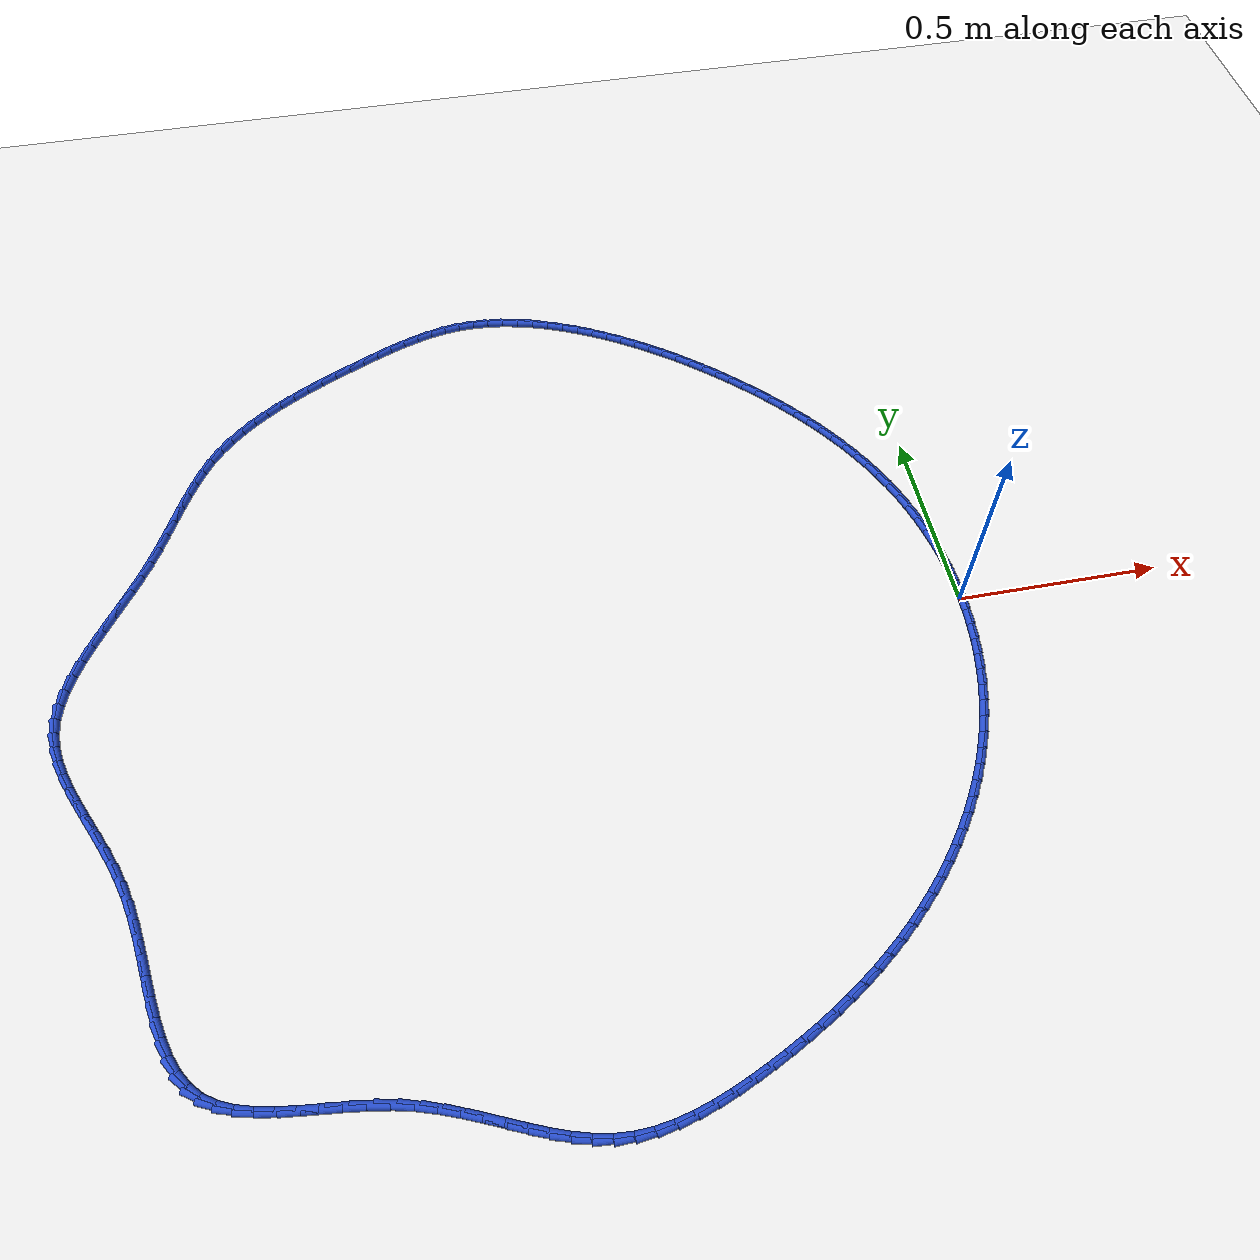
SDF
<sdf version="1.6">
 <world name="default">
  <light name="sun" type="directional">
   <pose>0 0 10 0 -0 0</pose>
   <diffuse>0.8 0.8 0.8 1</diffuse>
   <specular>0.2 0.2 0.2 1</specular>
   <attenuation>
    <range>1000</range>
    <constant>0.9</constant>
    <linear>0.01</linear>
    <quadratic>0.001</quadratic>
   </attenuation>
   <direction>-0.5 0.1 -0.9</direction>
  </light>
  <model name="ground_plane">
   <static>1</static>
   <link name="link">
    <collision name="collision">
     <geometry><plane><normal>0 0 1</normal><size>100 100</size></plane></geometry>
     <surface><friction><ode><mu>100</mu><mu2>50</mu2></ode></friction></surface>
    </collision>
    <visual name="visual">
     <cast_shadows>0</cast_shadows>
     <geometry><plane><normal>0 0 1</normal><size>100 100</size></plane></geometry>
     <material>
      <script><uri>file://media/materials/scripts/gazebo.material</uri><name>Gazebo/WhiteGlow</name></script>
     </material>
    </visual>
   </link>
  </model>
  <gravity>0 0 -9.8</gravity>
  <magnetic_field>6e-06 2.3e-05 -4.2e-05</magnetic_field>
  <atmosphere type="adiabatic"/>
  <physics name="default_physics" default="0" type="ode">
   <max_step_size>0.001</max_step_size>
   <real_time_factor>1</real_time_factor>
   <real_time_update_rate>1000</real_time_update_rate>
  </physics>
  <scene><ambient>0.4 0.4 0.4 1</ambient><background>0.7 0.7 0.7 1</background><shadows>1</shadows></scene>
  <spherical_coordinates>
   <surface_model>EARTH_WGS84</surface_model>
   <latitude_deg>0</latitude_deg>
   <longitude_deg>0</longitude_deg>
   <elevation>0</elevation>
   <heading_deg>0</heading_deg>
  </spherical_coordinates>
  <model name="line">
   <link name="link_0">
    <pose>-3.469446951953614e-18 -2.7755575615628914e-17 0.01 0 1.57 -1.5496947018431078</pose>
    <collision name="collision">
     <geometry><cylinder><radius>0.01</radius><length>0.08</length></cylinder></geometry>
    </collision>
    <visual name="visual">
     <material>
      <script><name>Gazebo/Blue</name><uri>file://media/materials/scripts/gazebo.material</uri></script>
     </material>
     <geometry><cylinder><radius>0.01</radius><length>0.08</length></cylinder></geometry>
    </visual>
   </link>
   <link name="link_1">
    <pose>-0.0008917149829064989 0.04225184682010225 0.01 0 1.57 -1.507987470645882</pose>
    <collision name="collision">
     <geometry><cylinder><radius>0.01</radius><length>0.08</length></cylinder></geometry>
    </collision>
    <visual name="visual">
     <material>
      <script><name>Gazebo/Blue</name><uri>file://media/materials/scripts/gazebo.material</uri></script>
     </material>
     <geometry><cylinder><radius>0.01</radius><length>0.08</length></cylinder></geometry>
    </visual>
   </link>
   <link name="link_2">
    <pose>-0.003544431993051579 0.08443105488146378 0.01 0 1.57 -1.4662126143395446</pose>
    <collision name="collision">
     <geometry><cylinder><radius>0.01</radius><length>0.08</length></cylinder></geometry>
    </collision>
    <visual name="visual">
     <material>
      <script><name>Gazebo/Blue</name><uri>file://media/materials/scripts/gazebo.material</uri></script>
     </material>
     <geometry><cylinder><radius>0.01</radius><length>0.08</length></cylinder></geometry>
    </visual>
   </link>
   <link name="link_3">
    <pose>-0.007955623263167566 0.1264557314520991 0.01 0 1.57 -1.4242733198361823</pose>
    <collision name="collision">
     <geometry><cylinder><radius>0.01</radius><length>0.08</length></cylinder></geometry>
    </collision>
    <visual name="visual">
     <material>
      <script><name>Gazebo/Blue</name><uri>file://media/materials/scripts/gazebo.material</uri></script>
     </material>
     <geometry><cylinder><radius>0.01</radius><length>0.08</length></cylinder></geometry>
    </visual>
   </link>
   <link name="link_4">
    <pose>-0.014122761025986754 0.16824398380002256 0.01 0 1.57 -1.3820740800271367</pose>
    <collision name="collision">
     <geometry><cylinder><radius>0.01</radius><length>0.08</length></cylinder></geometry>
    </collision>
    <visual name="visual">
     <material>
      <script><name>Gazebo/Blue</name><uri>file://media/materials/scripts/gazebo.material</uri></script>
     </material>
     <geometry><cylinder><radius>0.01</radius><length>0.08</length></cylinder></geometry>
    </visual>
   </link>
   <link name="link_5">
    <pose>-0.02204331751424147 0.2097139191932487 0.01 0 1.57 -1.3395214974619023</pose>
    <collision name="collision">
     <geometry><cylinder><radius>0.01</radius><length>0.08</length></cylinder></geometry>
    </collision>
    <visual name="visual">
     <material>
      <script><name>Gazebo/Blue</name><uri>file://media/materials/scripts/gazebo.material</uri></script>
     </material>
     <geometry><cylinder><radius>0.01</radius><length>0.08</length></cylinder></geometry>
    </visual>
   </link>
   <link name="link_6">
    <pose>-0.03171476496066401 0.25078364489979194 0.01 0 1.57 -1.2965251851470005</pose>
    <collision name="collision">
     <geometry><cylinder><radius>0.01</radius><length>0.08</length></cylinder></geometry>
    </collision>
    <visual name="visual">
     <material>
      <script><name>Gazebo/Blue</name><uri>file://media/materials/scripts/gazebo.material</uri></script>
     </material>
     <geometry><cylinder><radius>0.01</radius><length>0.08</length></cylinder></geometry>
    </visual>
   </link>
   <link name="link_7">
    <pose>-0.04313457559798668 0.2913712681876667 0.01 0 1.57 -1.2529987964605125</pose>
    <collision name="collision">
     <geometry><cylinder><radius>0.01</radius><length>0.08</length></cylinder></geometry>
    </collision>
    <visual name="visual">
     <material>
      <script><name>Gazebo/Blue</name><uri>file://media/materials/scripts/gazebo.material</uri></script>
     </material>
     <geometry><cylinder><radius>0.01</radius><length>0.08</length></cylinder></geometry>
    </visual>
   </link>
   <link name="link_8">
    <pose>-0.0563002216589418 0.33139489632488744 0.01 0 1.57 -1.208861211700292</pose>
    <collision name="collision">
     <geometry><cylinder><radius>0.01</radius><length>0.08</length></cylinder></geometry>
    </collision>
    <visual name="visual">
     <material>
      <script><name>Gazebo/Blue</name><uri>file://media/materials/scripts/gazebo.material</uri></script>
     </material>
     <geometry><cylinder><radius>0.01</radius><length>0.08</length></cylinder></geometry>
    </visual>
   </link>
   <link name="link_9">
    <pose>-0.07120917537626167 0.3707726365794687 0.01 0 1.57 -1.1641908299851473</pose>
    <collision name="collision">
     <geometry><cylinder><radius>0.01</radius><length>0.08</length></cylinder></geometry>
    </collision>
    <visual name="visual">
     <material>
      <script><name>Gazebo/Blue</name><uri>file://media/materials/scripts/gazebo.material</uri></script>
     </material>
     <geometry><cylinder><radius>0.01</radius><length>0.08</length></cylinder></geometry>
    </visual>
   </link>
   <link name="link_10">
    <pose>-0.08785375197273362 0.40942689265982 0.01 0 1.57 -1.120559447956313</pose>
    <collision name="collision">
     <geometry><cylinder><radius>0.01</radius><length>0.08</length></cylinder></geometry>
    </collision>
    <visual name="visual">
     <material>
      <script><name>Gazebo/Blue</name><uri>file://media/materials/scripts/gazebo.material</uri></script>
     </material>
     <geometry><cylinder><radius>0.01</radius><length>0.08</length></cylinder></geometry>
    </visual>
   </link>
   <link name="link_11">
    <pose>-0.10617188093022237 0.44732537846314824 0.01 0 1.57 -1.078948379894648</pose>
    <collision name="collision">
     <geometry><cylinder><radius>0.01</radius><length>0.08</length></cylinder></geometry>
    </collision>
    <visual name="visual">
     <material>
      <script><name>Gazebo/Blue</name><uri>file://media/materials/scripts/gazebo.material</uri></script>
     </material>
     <geometry><cylinder><radius>0.01</radius><length>0.08</length></cylinder></geometry>
    </visual>
   </link>
   <link name="link_12">
    <pose>-0.1260688775343158 0.48446297962994544 0.01 0 1.57 -1.0393693031894846</pose>
    <collision name="collision">
     <geometry><cylinder><radius>0.01</radius><length>0.08</length></cylinder></geometry>
    </collision>
    <visual name="visual">
     <material>
      <script><name>Gazebo/Blue</name><uri>file://media/materials/scripts/gazebo.material</uri></script>
     </material>
     <geometry><cylinder><radius>0.01</radius><length>0.08</length></cylinder></geometry>
    </visual>
   </link>
   <link name="link_13">
    <pose>-0.14744961454976055 0.5208349504764361 0.01 0 1.57 -1.0017954590820315</pose>
    <collision name="collision">
     <geometry><cylinder><radius>0.01</radius><length>0.08</length></cylinder></geometry>
    </collision>
    <visual name="visual">
     <material>
      <script><name>Gazebo/Blue</name><uri>file://media/materials/scripts/gazebo.material</uri></script>
     </material>
     <geometry><cylinder><radius>0.01</radius><length>0.08</length></cylinder></geometry>
    </visual>
   </link>
   <link name="link_14">
    <pose>-0.17021896474130332 0.5564365453188453 0.01 0 1.57 -0.9661800652637308</pose>
    <collision name="collision">
     <geometry><cylinder><radius>0.01</radius><length>0.08</length></cylinder></geometry>
    </collision>
    <visual name="visual">
     <material>
      <script><name>Gazebo/Blue</name><uri>file://media/materials/scripts/gazebo.material</uri></script>
     </material>
     <geometry><cylinder><radius>0.01</radius><length>0.08</length></cylinder></geometry>
    </visual>
   </link>
   <link name="link_15">
    <pose>-0.19428180087369062 0.5912630184733974 0.01 0 1.57 -0.9324611764683312</pose>
    <collision name="collision">
     <geometry><cylinder><radius>0.01</radius><length>0.08</length></cylinder></geometry>
    </collision>
    <visual name="visual">
     <material>
      <script><name>Gazebo/Blue</name><uri>file://media/materials/scripts/gazebo.material</uri></script>
     </material>
     <geometry><cylinder><radius>0.01</radius><length>0.08</length></cylinder></geometry>
    </visual>
   </link>
   <link name="link_16">
    <pose>-0.21954299571166902 0.6253096242563165 0.01 0 1.57 -0.900565969145883</pose>
    <collision name="collision">
     <geometry><cylinder><radius>0.01</radius><length>0.08</length></cylinder></geometry>
    </collision>
    <visual name="visual">
     <material>
      <script><name>Gazebo/Blue</name><uri>file://media/materials/scripts/gazebo.material</uri></script>
     </material>
     <geometry><cylinder><radius>0.01</radius><length>0.08</length></cylinder></geometry>
    </visual>
   </link>
   <link name="link_17">
    <pose>-0.24590742201998533 0.6585716169838282 0.01 0 1.57 -0.8704143902009182</pose>
    <collision name="collision">
     <geometry><cylinder><radius>0.01</radius><length>0.08</length></cylinder></geometry>
    </collision>
    <visual name="visual">
     <material>
      <script><name>Gazebo/Blue</name><uri>file://media/materials/scripts/gazebo.material</uri></script>
     </material>
     <geometry><cylinder><radius>0.01</radius><length>0.08</length></cylinder></geometry>
    </visual>
   </link>
   <link name="link_18">
    <pose>-0.2732799525633859 0.6910442509721563 0.01 0 1.57 -0.8419221715945242</pose>
    <collision name="collision">
     <geometry><cylinder><radius>0.01</radius><length>0.08</length></cylinder></geometry>
    </collision>
    <visual name="visual">
     <material>
      <script><name>Gazebo/Blue</name><uri>file://media/materials/scripts/gazebo.material</uri></script>
     </material>
     <geometry><cylinder><radius>0.01</radius><length>0.08</length></cylinder></geometry>
    </visual>
   </link>
   <link name="link_19">
    <pose>-0.3015654601066175 0.7227227805375258 0.01 0 1.57 -0.8150032527196142</pose>
    <collision name="collision">
     <geometry><cylinder><radius>0.01</radius><length>0.08</length></cylinder></geometry>
    </collision>
    <visual name="visual">
     <material>
      <script><name>Gazebo/Blue</name><uri>file://media/materials/scripts/gazebo.material</uri></script>
     </material>
     <geometry><cylinder><radius>0.01</radius><length>0.08</length></cylinder></geometry>
    </visual>
   </link>
   <link name="link_20">
    <pose>-0.3306688174144268 0.7536024599961615 0.01 0 1.57 -0.7895716750842159</pose>
    <collision name="collision">
     <geometry><cylinder><radius>0.01</radius><length>0.08</length></cylinder></geometry>
    </collision>
    <visual name="visual">
     <material>
      <script><name>Gazebo/Blue</name><uri>file://media/materials/scripts/gazebo.material</uri></script>
     </material>
     <geometry><cylinder><radius>0.01</radius><length>0.08</length></cylinder></geometry>
    </visual>
   </link>
   <link name="link_21">
    <pose>-0.3604948972515602 0.7836785436642874 0.01 0 1.57 -0.7655430235785317</pose>
    <collision name="collision">
     <geometry><cylinder><radius>0.01</radius><length>0.08</length></cylinder></geometry>
    </collision>
    <visual name="visual">
     <material>
      <script><name>Gazebo/Blue</name><uri>file://media/materials/scripts/gazebo.material</uri></script>
     </material>
     <geometry><cylinder><radius>0.01</radius><length>0.08</length></cylinder></geometry>
    </visual>
   </link>
   <link name="link_22">
    <pose>-0.3909485723827645 0.8129462858581288 0.01 0 1.57 -0.742835489616907</pose>
    <collision name="collision">
     <geometry><cylinder><radius>0.01</radius><length>0.08</length></cylinder></geometry>
    </collision>
    <visual name="visual">
     <material>
      <script><name>Gazebo/Blue</name><uri>file://media/materials/scripts/gazebo.material</uri></script>
     </material>
     <geometry><cylinder><radius>0.01</radius><length>0.08</length></cylinder></geometry>
    </visual>
   </link>
   <link name="link_23">
    <pose>-0.42193471557278617 0.8414009408939098 0.01 0 1.57 -0.7212509171712825</pose>
    <collision name="collision">
     <geometry><cylinder><radius>0.01</radius><length>0.08</length></cylinder></geometry>
    </collision>
    <visual name="visual">
     <material>
      <script><name>Gazebo/Blue</name><uri>file://media/materials/scripts/gazebo.material</uri></script>
     </material>
     <geometry><cylinder><radius>0.01</radius><length>0.08</length></cylinder></geometry>
    </visual>
   </link>
   <link name="link_24">
    <pose>-0.45336688381607915 0.869038728261463 0.01 0 1.57 -0.6990263947751288</pose>
    <collision name="collision">
     <geometry><cylinder><radius>0.01</radius><length>0.08</length></cylinder></geometry>
    </collision>
    <visual name="visual">
     <material>
      <script><name>Gazebo/Blue</name><uri>file://media/materials/scripts/gazebo.material</uri></script>
     </material>
     <geometry><cylinder><radius>0.01</radius><length>0.08</length></cylinder></geometry>
    </visual>
   </link>
   <link name="link_25">
    <pose>-0.48528500544045994 0.8958699124816509 0.01 0 1.57 -0.6750007257451784</pose>
    <collision name="collision">
     <geometry><cylinder><radius>0.01</radius><length>0.08</length></cylinder></geometry>
    </collision>
    <visual name="visual">
     <material>
      <script><name>Gazebo/Blue</name><uri>file://media/materials/scripts/gazebo.material</uri></script>
     </material>
     <geometry><cylinder><radius>0.01</radius><length>0.08</length></cylinder></geometry>
    </visual>
   </link>
   <link name="link_26">
    <pose>-0.5178244953026235 0.9219153705396154 0.01 0 1.57 -0.6493736781397184</pose>
    <collision name="collision">
     <geometry><cylinder><radius>0.01</radius><length>0.08</length></cylinder></geometry>
    </collision>
    <visual name="visual">
     <material>
      <script><name>Gazebo/Blue</name><uri>file://media/materials/scripts/gazebo.material</uri></script>
     </material>
     <geometry><cylinder><radius>0.01</radius><length>0.08</length></cylinder></geometry>
    </visual>
   </link>
   <link name="link_27">
    <pose>-0.5511231230595295 0.9471962411352546 0.01 0 1.57 -0.6224156574424398</pose>
    <collision name="collision">
     <geometry><cylinder><radius>0.01</radius><length>0.08</length></cylinder></geometry>
    </collision>
    <visual name="visual">
     <material>
      <script><name>Gazebo/Blue</name><uri>file://media/materials/scripts/gazebo.material</uri></script>
     </material>
     <geometry><cylinder><radius>0.01</radius><length>0.08</length></cylinder></geometry>
    </visual>
   </link>
   <link name="link_28">
    <pose>-0.5853186583681362 0.9717336629684663 0.01 0 1.57 -0.5944263656051536</pose>
    <collision name="collision">
     <geometry><cylinder><radius>0.01</radius><length>0.08</length></cylinder></geometry>
    </collision>
    <visual name="visual">
     <material>
      <script><name>Gazebo/Blue</name><uri>file://media/materials/scripts/gazebo.material</uri></script>
     </material>
     <geometry><cylinder><radius>0.01</radius><length>0.08</length></cylinder></geometry>
    </visual>
   </link>
   <link name="link_29">
    <pose>-0.6205488708854036 0.9955487747391487 0.01 0 1.57 -0.5654877578045786</pose>
    <collision name="collision">
     <geometry><cylinder><radius>0.01</radius><length>0.08</length></cylinder></geometry>
    </collision>
    <visual name="visual">
     <material>
      <script><name>Gazebo/Blue</name><uri>file://media/materials/scripts/gazebo.material</uri></script>
     </material>
     <geometry><cylinder><radius>0.01</radius><length>0.08</length></cylinder></geometry>
    </visual>
   </link>
   <link name="link_30">
    <pose>-0.6569225371076504 1.018632260359022 0.01 0 1.57 -0.5342623128314363</pose>
    <collision name="collision">
     <geometry><cylinder><radius>0.01</radius><length>0.08</length></cylinder></geometry>
    </collision>
    <visual name="visual">
     <material>
      <script><name>Gazebo/Blue</name><uri>file://media/materials/scripts/gazebo.material</uri></script>
     </material>
     <geometry><cylinder><radius>0.01</radius><length>0.08</length></cylinder></geometry>
    </visual>
   </link>
   <link name="link_31">
    <pose>-0.6943720421616941 1.0407895199805977 0.01 0 1.57 -0.4998683663550835</pose>
    <collision name="collision">
     <geometry><cylinder><radius>0.01</radius><length>0.08</length></cylinder></geometry>
    </collision>
    <visual name="visual">
     <material>
      <script><name>Gazebo/Blue</name><uri>file://media/materials/scripts/gazebo.material</uri></script>
     </material>
     <geometry><cylinder><radius>0.01</radius><length>0.08</length></cylinder></geometry>
    </visual>
   </link>
   <link name="link_32">
    <pose>-0.7327634324893593 1.0617562707499502 0.01 0 1.57 -0.46185478783518247</pose>
    <collision name="collision">
     <geometry><cylinder><radius>0.01</radius><length>0.08</length></cylinder></geometry>
    </collision>
    <visual name="visual">
     <material>
      <script><name>Gazebo/Blue</name><uri>file://media/materials/scripts/gazebo.material</uri></script>
     </material>
     <geometry><cylinder><radius>0.01</radius><length>0.08</length></cylinder></geometry>
    </visual>
   </link>
   <link name="link_33">
    <pose>-0.7719626347876547 1.0812681040316634 0.01 0 1.57 -0.419714470521365</pose>
    <collision name="collision">
     <geometry><cylinder><radius>0.01</radius><length>0.08</length></cylinder></geometry>
    </collision>
    <visual name="visual">
     <material>
      <script><name>Gazebo/Blue</name><uri>file://media/materials/scripts/gazebo.material</uri></script>
     </material>
     <geometry><cylinder><radius>0.01</radius><length>0.08</length></cylinder></geometry>
    </visual>
   </link>
   <link name="link_34">
    <pose>-0.8118355757535893 1.0990606111903205 0.01 0 1.57 -0.37288350924930824</pose>
    <collision name="collision">
     <geometry><cylinder><radius>0.01</radius><length>0.08</length></cylinder></geometry>
    </collision>
    <visual name="visual">
     <material>
      <script><name>Gazebo/Blue</name><uri>file://media/materials/scripts/gazebo.material</uri></script>
     </material>
     <geometry><cylinder><radius>0.01</radius><length>0.08</length></cylinder></geometry>
    </visual>
   </link>
   <link name="link_35">
    <pose>-0.8522481820841725 1.1148693835905052 0.01 0 1.57 -0.32074837740846524</pose>
    <collision name="collision">
     <geometry><cylinder><radius>0.01</radius><length>0.08</length></cylinder></geometry>
    </collision>
    <visual name="visual">
     <material>
      <script><name>Gazebo/Blue</name><uri>file://media/materials/scripts/gazebo.material</uri></script>
     </material>
     <geometry><cylinder><radius>0.01</radius><length>0.08</length></cylinder></geometry>
    </visual>
   </link>
   <link name="link_36">
    <pose>-0.8930663804764135 1.1284300125968012 0.01 0 1.57 -0.26266477723516907</pose>
    <collision name="collision">
     <geometry><cylinder><radius>0.01</radius><length>0.08</length></cylinder></geometry>
    </collision>
    <visual name="visual">
     <material>
      <script><name>Gazebo/Blue</name><uri>file://media/materials/scripts/gazebo.material</uri></script>
     </material>
     <geometry><cylinder><radius>0.01</radius><length>0.08</length></cylinder></geometry>
    </visual>
   </link>
   <link name="link_37">
    <pose>-0.9341560976273213 1.1394780895737922 0.01 0 1.57 -0.19799450942579938</pose>
    <collision name="collision">
     <geometry><cylinder><radius>0.01</radius><length>0.08</length></cylinder></geometry>
    </collision>
    <visual name="visual">
     <material>
      <script><name>Gazebo/Blue</name><uri>file://media/materials/scripts/gazebo.material</uri></script>
     </material>
     <geometry><cylinder><radius>0.01</radius><length>0.08</length></cylinder></geometry>
    </visual>
   </link>
   <link name="link_38">
    <pose>-0.975383260233905 1.1477492058860612 0.01 0 1.57 -0.12616784969773842</pose>
    <collision name="collision">
     <geometry><cylinder><radius>0.01</radius><length>0.08</length></cylinder></geometry>
    </collision>
    <visual name="visual">
     <material>
      <script><name>Gazebo/Blue</name><uri>file://media/materials/scripts/gazebo.material</uri></script>
     </material>
     <geometry><cylinder><radius>0.01</radius><length>0.08</length></cylinder></geometry>
    </visual>
   </link>
   <link name="link_39">
    <pose>-1.016613794993174 1.152978952898192 0.01 0 1.57 -0.04677793984952982</pose>
    <collision name="collision">
     <geometry><cylinder><radius>0.01</radius><length>0.08</length></cylinder></geometry>
    </collision>
    <visual name="visual">
     <material>
      <script><name>Gazebo/Blue</name><uri>file://media/materials/scripts/gazebo.material</uri></script>
     </material>
     <geometry><cylinder><radius>0.01</radius><length>0.08</length></cylinder></geometry>
    </visual>
   </link>
   <link name="link_40">
    <pose>-1.0577136286021367 1.154902921974768 0.01 0 1.57 0.04029200847532528</pose>
    <collision name="collision">
     <geometry><cylinder><radius>0.01</radius><length>0.08</length></cylinder></geometry>
    </collision>
    <visual name="visual">
     <material>
      <script><name>Gazebo/Blue</name><uri>file://media/materials/scripts/gazebo.material</uri></script>
     </material>
     <geometry><cylinder><radius>0.01</radius><length>0.08</length></cylinder></geometry>
    </visual>
   </link>
   <link name="link_41">
    <pose>-1.0985486877578032 1.1532567044803732 0.01 0 1.57 0.13213787029776297</pose>
    <collision name="collision">
     <geometry><cylinder><radius>0.01</radius><length>0.08</length></cylinder></geometry>
    </collision>
    <visual name="visual">
     <material>
      <script><name>Gazebo/Blue</name><uri>file://media/materials/scripts/gazebo.material</uri></script>
     </material>
     <geometry><cylinder><radius>0.01</radius><length>0.08</length></cylinder></geometry>
    </visual>
   </link>
   <link name="link_42">
    <pose>-1.1390123178358764 1.1478785886999863 0.01 0 1.57 0.21524728273505536</pose>
    <collision name="collision">
     <geometry><cylinder><radius>0.01</radius><length>0.08</length></cylinder></geometry>
    </collision>
    <visual name="visual">
     <material>
      <script><name>Gazebo/Blue</name><uri>file://media/materials/scripts/gazebo.material</uri></script>
     </material>
     <geometry><cylinder><radius>0.01</radius><length>0.08</length></cylinder></geometry>
    </visual>
   </link>
   <link name="link_43">
    <pose>-1.179131440031456 1.1391071724135908 0.01 0 1.57 0.2850279630217975</pose>
    <collision name="collision">
     <geometry><cylinder><radius>0.01</radius><length>0.08</length></cylinder></geometry>
    </collision>
    <visual name="visual">
     <material>
      <script><name>Gazebo/Blue</name><uri>file://media/materials/scripts/gazebo.material</uri></script>
     </material>
     <geometry><cylinder><radius>0.01</radius><length>0.08</length></cylinder></geometry>
    </visual>
   </link>
   <link name="link_44">
    <pose>-1.2189735923553477 1.127433184068576 0.01 0 1.57 0.34148465113643794</pose>
    <collision name="collision">
     <geometry><cylinder><radius>0.01</radius><length>0.08</length></cylinder></geometry>
    </collision>
    <visual name="visual">
     <material>
      <script><name>Gazebo/Blue</name><uri>file://media/materials/scripts/gazebo.material</uri></script>
     </material>
     <geometry><cylinder><radius>0.01</radius><length>0.08</length></cylinder></geometry>
    </visual>
   </link>
   <link name="link_45">
    <pose>-1.2586063222847301 1.1133473875687294 0.01 0 1.57 0.3850930146785881</pose>
    <collision name="collision">
     <geometry><cylinder><radius>0.01</radius><length>0.08</length></cylinder></geometry>
    </collision>
    <visual name="visual">
     <material>
      <script><name>Gazebo/Blue</name><uri>file://media/materials/scripts/gazebo.material</uri></script>
     </material>
     <geometry><cylinder><radius>0.01</radius><length>0.08</length></cylinder></geometry>
    </visual>
   </link>
   <link name="link_46">
    <pose>-1.2980971772967849 1.0973405468178385 0.01 0 1.57 0.41649989035423574</pose>
    <collision name="collision">
     <geometry><cylinder><radius>0.01</radius><length>0.08</length></cylinder></geometry>
    </collision>
    <visual name="visual">
     <material>
      <script><name>Gazebo/Blue</name><uri>file://media/materials/scripts/gazebo.material</uri></script>
     </material>
     <geometry><cylinder><radius>0.01</radius><length>0.08</length></cylinder></geometry>
    </visual>
   </link>
   <link name="link_47">
    <pose>-1.3375137048686905 1.079903425719691 0.01 0 1.57 0.4363233595991484</pose>
    <collision name="collision">
     <geometry><cylinder><radius>0.01</radius><length>0.08</length></cylinder></geometry>
    </collision>
    <visual name="visual">
     <material>
      <script><name>Gazebo/Blue</name><uri>file://media/materials/scripts/gazebo.material</uri></script>
     </material>
     <geometry><cylinder><radius>0.01</radius><length>0.08</length></cylinder></geometry>
    </visual>
   </link>
   <link name="link_48">
    <pose>-1.3769234524776284 1.0615267881780728 0.01 0 1.57 0.4465400464991043</pose>
    <collision name="collision">
     <geometry><cylinder><radius>0.01</radius><length>0.08</length></cylinder></geometry>
    </collision>
    <visual name="visual">
     <material>
      <script><name>Gazebo/Blue</name><uri>file://media/materials/scripts/gazebo.material</uri></script>
     </material>
     <geometry><cylinder><radius>0.01</radius><length>0.08</length></cylinder></geometry>
    </visual>
   </link>
   <link name="link_49">
    <pose>-1.416364322015859 1.042642702480539 0.01 0 1.57 0.45775210390355414</pose>
    <collision name="collision">
     <geometry><cylinder><radius>0.01</radius><length>0.08</length></cylinder></geometry>
    </collision>
    <visual name="visual">
     <material>
      <script><name>Gazebo/Blue</name><uri>file://media/materials/scripts/gazebo.material</uri></script>
     </material>
     <geometry><cylinder><radius>0.01</radius><length>0.08</length></cylinder></geometry>
    </visual>
   </link>
   <link name="link_50">
    <pose>-1.455669905100056 1.0232787207763443 0.01 0 1.57 0.47443972566426673</pose>
    <collision name="collision">
     <geometry><cylinder><radius>0.01</radius><length>0.08</length></cylinder></geometry>
    </collision>
    <visual name="visual">
     <material>
      <script><name>Gazebo/Blue</name><uri>file://media/materials/scripts/gazebo.material</uri></script>
     </material>
     <geometry><cylinder><radius>0.01</radius><length>0.08</length></cylinder></geometry>
    </visual>
   </link>
   <link name="link_51">
    <pose>-1.4945877038483149 1.003291945679537 0.01 0 1.57 0.4968179873094166</pose>
    <collision name="collision">
     <geometry><cylinder><radius>0.01</radius><length>0.08</length></cylinder></geometry>
    </collision>
    <visual name="visual">
     <material>
      <script><name>Gazebo/Blue</name><uri>file://media/materials/scripts/gazebo.material</uri></script>
     </material>
     <geometry><cylinder><radius>0.01</radius><length>0.08</length></cylinder></geometry>
    </visual>
   </link>
   <link name="link_52">
    <pose>-1.5328649188666017 0.982538882837018 0.01 0 1.57 0.5251878328590559</pose>
    <collision name="collision">
     <geometry><cylinder><radius>0.01</radius><length>0.08</length></cylinder></geometry>
    </collision>
    <visual name="visual">
     <material>
      <script><name>Gazebo/Blue</name><uri>file://media/materials/scripts/gazebo.material</uri></script>
     </material>
     <geometry><cylinder><radius>0.01</radius><length>0.08</length></cylinder></geometry>
    </visual>
   </link>
   <link name="link_53">
    <pose>-1.570248750760882 0.9608760378956859 0.01 0 1.57 0.5599394599012931</pose>
    <collision name="collision">
     <geometry><cylinder><radius>0.01</radius><length>0.08</length></cylinder></geometry>
    </collision>
    <visual name="visual">
     <material>
      <script><name>Gazebo/Blue</name><uri>file://media/materials/scripts/gazebo.material</uri></script>
     </material>
     <geometry><cylinder><radius>0.01</radius><length>0.08</length></cylinder></geometry>
    </visual>
   </link>
   <link name="link_54">
    <pose>-1.6064864001371204 0.9381599165024402 0.01 0 1.57 0.6015328103334711</pose>
    <collision name="collision">
     <geometry><cylinder><radius>0.01</radius><length>0.08</length></cylinder></geometry>
    </collision>
    <visual name="visual">
     <material>
      <script><name>Gazebo/Blue</name><uri>file://media/materials/scripts/gazebo.material</uri></script>
     </material>
     <geometry><cylinder><radius>0.01</radius><length>0.08</length></cylinder></geometry>
    </visual>
   </link>
   <link name="link_55">
    <pose>-1.6413250676012823 0.9142470243041803 0.01 0 1.57 0.6504646513402169</pose>
    <collision name="collision">
     <geometry><cylinder><radius>0.01</radius><length>0.08</length></cylinder></geometry>
    </collision>
    <visual name="visual">
     <material>
      <script><name>Gazebo/Blue</name><uri>file://media/materials/scripts/gazebo.material</uri></script>
     </material>
     <geometry><cylinder><radius>0.01</radius><length>0.08</length></cylinder></geometry>
    </visual>
   </link>
   <link name="link_56">
    <pose>-1.6745119537593334 0.888993866947805 0.01 0 1.57 0.7072150500660427</pose>
    <collision name="collision">
     <geometry><cylinder><radius>0.01</radius><length>0.08</length></cylinder></geometry>
    </collision>
    <visual name="visual">
     <material>
      <script><name>Gazebo/Blue</name><uri>file://media/materials/scripts/gazebo.material</uri></script>
     </material>
     <geometry><cylinder><radius>0.01</radius><length>0.08</length></cylinder></geometry>
    </visual>
   </link>
   <link name="link_57">
    <pose>-1.7057942592172388 0.8622569500802147 0.01 0 1.57 0.7721659109851984</pose>
    <collision name="collision">
     <geometry><cylinder><radius>0.01</radius><length>0.08</length></cylinder></geometry>
    </collision>
    <visual name="visual">
     <material>
      <script><name>Gazebo/Blue</name><uri>file://media/materials/scripts/gazebo.material</uri></script>
     </material>
     <geometry><cylinder><radius>0.01</radius><length>0.08</length></cylinder></geometry>
    </visual>
   </link>
   <link name="link_58">
    <pose>-1.7349191845809644 0.8338927793483081 0.01 0 1.57 0.8454874473303543</pose>
    <collision name="collision">
     <geometry><cylinder><radius>0.01</radius><length>0.08</length></cylinder></geometry>
    </collision>
    <visual name="visual">
     <material>
      <script><name>Gazebo/Blue</name><uri>file://media/materials/scripts/gazebo.material</uri></script>
     </material>
     <geometry><cylinder><radius>0.01</radius><length>0.08</length></cylinder></geometry>
    </visual>
   </link>
   <link name="link_59">
    <pose>-1.761633930456474 0.8037578603989848 0.01 0 1.57 0.9264124519732472</pose>
    <collision name="collision">
     <geometry><cylinder><radius>0.01</radius><length>0.08</length></cylinder></geometry>
    </collision>
    <visual name="visual">
     <material>
      <script><name>Gazebo/Blue</name><uri>file://media/materials/scripts/gazebo.material</uri></script>
     </material>
     <geometry><cylinder><radius>0.01</radius><length>0.08</length></cylinder></geometry>
    </visual>
   </link>
   <link name="link_60">
    <pose>-1.7857069150194433 0.7717195083017632 0.01 0 1.57 1.003297893461719</pose>
    <collision name="collision">
     <geometry><cylinder><radius>0.01</radius><length>0.08</length></cylinder></geometry>
    </collision>
    <visual name="visual">
     <material>
      <script><name>Gazebo/Blue</name><uri>file://media/materials/scripts/gazebo.material</uri></script>
     </material>
     <geometry><cylinder><radius>0.01</radius><length>0.08</length></cylinder></geometry>
    </visual>
   </link>
   <link name="link_61">
    <pose>-1.8072998043067303 0.7378453806905475 0.01 0 1.57 1.0654611247885744</pose>
    <collision name="collision">
     <geometry><cylinder><radius>0.01</radius><length>0.08</length></cylinder></geometry>
    </collision>
    <visual name="visual">
     <material>
      <script><name>Gazebo/Blue</name><uri>file://media/materials/scripts/gazebo.material</uri></script>
     </material>
     <geometry><cylinder><radius>0.01</radius><length>0.08</length></cylinder></geometry>
    </visual>
   </link>
   <link name="link_62">
    <pose>-1.8269211223273498 0.7023798441466508 0.01 0 1.57 1.1122279318529793</pose>
    <collision name="collision">
     <geometry><cylinder><radius>0.01</radius><length>0.08</length></cylinder></geometry>
    </collision>
    <visual name="visual">
     <material>
      <script><name>Gazebo/Blue</name><uri>file://media/materials/scripts/gazebo.material</uri></script>
     </material>
     <geometry><cylinder><radius>0.01</radius><length>0.08</length></cylinder></geometry>
    </visual>
   </link>
   <link name="link_63">
    <pose>-1.8450912868313056 0.6655733245915731 0.01 0 1.57 1.1438739753772107</pose>
    <collision name="collision">
     <geometry><cylinder><radius>0.01</radius><length>0.08</length></cylinder></geometry>
    </collision>
    <visual name="visual">
     <material>
      <script><name>Gazebo/Blue</name><uri>file://media/materials/scripts/gazebo.material</uri></script>
     </material>
     <geometry><cylinder><radius>0.01</radius><length>0.08</length></cylinder></geometry>
    </visual>
   </link>
   <link name="link_64">
    <pose>-1.8623307155686009 0.627676247946817 0.01 0 1.57 1.1609545962941024</pose>
    <collision name="collision">
     <geometry><cylinder><radius>0.01</radius><length>0.08</length></cylinder></geometry>
    </collision>
    <visual name="visual">
     <material>
      <script><name>Gazebo/Blue</name><uri>file://media/materials/scripts/gazebo.material</uri></script>
     </material>
     <geometry><cylinder><radius>0.01</radius><length>0.08</length></cylinder></geometry>
    </visual>
   </link>
   <link name="link_65">
    <pose>-1.8791598262892375 0.5889390401338824 0.01 0 1.57 1.1640838647126117</pose>
    <collision name="collision">
     <geometry><cylinder><radius>0.01</radius><length>0.08</length></cylinder></geometry>
    </collision>
    <visual name="visual">
     <material>
      <script><name>Gazebo/Blue</name><uri>file://media/materials/scripts/gazebo.material</uri></script>
     </material>
     <geometry><cylinder><radius>0.01</radius><length>0.08</length></cylinder></geometry>
    </visual>
   </link>
   <link name="link_66">
    <pose>-1.8960990367432202 0.5496121270742709 0.01 0 1.57 1.1538293098801014</pose>
    <collision name="collision">
     <geometry><cylinder><radius>0.01</radius><length>0.08</length></cylinder></geometry>
    </collision>
    <visual name="visual">
     <material>
      <script><name>Gazebo/Blue</name><uri>file://media/materials/scripts/gazebo.material</uri></script>
     </material>
     <geometry><cylinder><radius>0.01</radius><length>0.08</length></cylinder></geometry>
    </visual>
   </link>
   <link name="link_67">
    <pose>-1.9136687646805495 0.5099459346894833 0.01 0 1.57 1.1306982845406508</pose>
    <collision name="collision">
     <geometry><cylinder><radius>0.01</radius><length>0.08</length></cylinder></geometry>
    </collision>
    <visual name="visual">
     <material>
      <script><name>Gazebo/Blue</name><uri>file://media/materials/scripts/gazebo.material</uri></script>
     </material>
     <geometry><cylinder><radius>0.01</radius><length>0.08</length></cylinder></geometry>
    </visual>
   </link>
   <link name="link_68">
    <pose>-1.9323894278512306 0.47019088890102106 0.01 0 1.57 1.0955273490663542</pose>
    <collision name="collision">
     <geometry><cylinder><radius>0.01</radius><length>0.08</length></cylinder></geometry>
    </collision>
    <visual name="visual">
     <material>
      <script><name>Gazebo/Blue</name><uri>file://media/materials/scripts/gazebo.material</uri></script>
     </material>
     <geometry><cylinder><radius>0.01</radius><length>0.08</length></cylinder></geometry>
    </visual>
   </link>
   <link name="link_69">
    <pose>-1.9527663912154003 0.4305941588736135 0.01 0 1.57 1.0601092812304787</pose>
    <collision name="collision">
     <geometry><cylinder><radius>0.01</radius><length>0.08</length></cylinder></geometry>
    </collision>
    <visual name="visual">
     <material>
      <script><name>Gazebo/Blue</name><uri>file://media/materials/scripts/gazebo.material</uri></script>
     </material>
     <geometry><cylinder><radius>0.01</radius><length>0.08</length></cylinder></geometry>
    </visual>
   </link>
   <link name="link_70">
    <pose>-1.9747865650582377 0.39129074315187184 0.01 0 1.57 1.037849866012137</pose>
    <collision name="collision">
     <geometry><cylinder><radius>0.01</radius><length>0.08</length></cylinder></geometry>
    </collision>
    <visual name="visual">
     <material>
      <script><name>Gazebo/Blue</name><uri>file://media/materials/scripts/gazebo.material</uri></script>
     </material>
     <geometry><cylinder><radius>0.01</radius><length>0.08</length></cylinder></geometry>
    </visual>
   </link>
   <link name="link_71">
    <pose>-1.9977996109234377 0.35227776788778786 0.01 0 1.57 1.0289329674795495</pose>
    <collision name="collision">
     <geometry><cylinder><radius>0.01</radius><length>0.08</length></cylinder></geometry>
    </collision>
    <visual name="visual">
     <material>
      <script><name>Gazebo/Blue</name><uri>file://media/materials/scripts/gazebo.material</uri></script>
     </material>
     <geometry><cylinder><radius>0.01</radius><length>0.08</length></cylinder></geometry>
    </visual>
   </link>
   <link name="link_72">
    <pose>-2.0211160613007526 0.3135438934398003 0.01 0 1.57 1.0332352668993912</pose>
    <collision name="collision">
     <geometry><cylinder><radius>0.01</radius><length>0.08</length></cylinder></geometry>
    </collision>
    <visual name="visual">
     <material>
      <script><name>Gazebo/Blue</name><uri>file://media/materials/scripts/gazebo.material</uri></script>
     </material>
     <geometry><cylinder><radius>0.01</radius><length>0.08</length></cylinder></geometry>
    </visual>
   </link>
   <link name="link_73">
    <pose>-2.044046448679936 0.27507778016634676 0.01 0 1.57 1.0512409808345036</pose>
    <collision name="collision">
     <geometry><cylinder><radius>0.01</radius><length>0.08</length></cylinder></geometry>
    </collision>
    <visual name="visual">
     <material>
      <script><name>Gazebo/Blue</name><uri>file://media/materials/scripts/gazebo.material</uri></script>
     </material>
     <geometry><cylinder><radius>0.01</radius><length>0.08</length></cylinder></geometry>
    </visual>
   </link>
   <link name="link_74">
    <pose>-2.06590130555074 0.23686808842586585 0.01 0 1.57 1.0840833535541032</pose>
    <collision name="collision">
     <geometry><cylinder><radius>0.01</radius><length>0.08</length></cylinder></geometry>
    </collision>
    <visual name="visual">
     <material>
      <script><name>Gazebo/Blue</name><uri>file://media/materials/scripts/gazebo.material</uri></script>
     </material>
     <geometry><cylinder><radius>0.01</radius><length>0.08</length></cylinder></geometry>
    </visual>
   </link>
   <link name="link_75">
    <pose>-2.0859911644029183 0.1989034785767954 0.01 0 1.57 1.1335674551650337</pose>
    <collision name="collision">
     <geometry><cylinder><radius>0.01</radius><length>0.08</length></cylinder></geometry>
    </collision>
    <visual name="visual">
     <material>
      <script><name>Gazebo/Blue</name><uri>file://media/materials/scripts/gazebo.material</uri></script>
     </material>
     <geometry><cylinder><radius>0.01</radius><length>0.08</length></cylinder></geometry>
    </visual>
   </link>
   <link name="link_76">
    <pose>-2.103626557726223 0.16117261097757327 0.01 0 1.57 1.2021107853215651</pose>
    <collision name="collision">
     <geometry><cylinder><radius>0.01</radius><length>0.08</length></cylinder></geometry>
    </collision>
    <visual name="visual">
     <material>
      <script><name>Gazebo/Blue</name><uri>file://media/materials/scripts/gazebo.material</uri></script>
     </material>
     <geometry><cylinder><radius>0.01</radius><length>0.08</length></cylinder></geometry>
    </visual>
   </link>
   <link name="link_77">
    <pose>-2.118118018010408 0.1236641459866382 0.01 0 1.57 1.292455541089089</pose>
    <collision name="collision">
     <geometry><cylinder><radius>0.01</radius><length>0.08</length></cylinder></geometry>
    </collision>
    <visual name="visual">
     <material>
      <script><name>Gazebo/Blue</name><uri>file://media/materials/scripts/gazebo.material</uri></script>
     </material>
     <geometry><cylinder><radius>0.01</radius><length>0.08</length></cylinder></geometry>
    </visual>
   </link>
   <link name="link_78">
    <pose>-2.1287760777452256 0.08636674396242769 0.01 0 1.57 1.4069003903501907</pose>
    <collision name="collision">
     <geometry><cylinder><radius>0.01</radius><length>0.08</length></cylinder></geometry>
    </collision>
    <visual name="visual">
     <material>
      <script><name>Gazebo/Blue</name><uri>file://media/materials/scripts/gazebo.material</uri></script>
     </material>
     <geometry><cylinder><radius>0.01</radius><length>0.08</length></cylinder></geometry>
    </visual>
   </link>
   <link name="link_79">
    <pose>-2.1349112694204284 0.049269065263380485 0.01 0 1.57 1.545348507665284</pose>
    <collision name="collision">
     <geometry><cylinder><radius>0.01</radius><length>0.08</length></cylinder></geometry>
    </collision>
    <visual name="visual">
     <material>
      <script><name>Gazebo/Blue</name><uri>file://media/materials/scripts/gazebo.material</uri></script>
     </material>
     <geometry><cylinder><radius>0.01</radius><length>0.08</length></cylinder></geometry>
    </visual>
   </link>
   <link name="link_80">
    <pose>-2.1358507743011708 0.012358158985812195 0.01 0 1.57 -1.4539024838471586</pose>
    <collision name="collision">
     <geometry><cylinder><radius>0.01</radius><length>0.08</length></cylinder></geometry>
    </collision>
    <visual name="visual">
     <material>
      <script><name>Gazebo/Blue</name><uri>file://media/materials/scripts/gazebo.material</uri></script>
     </material>
     <geometry><cylinder><radius>0.01</radius><length>0.08</length></cylinder></geometry>
    </visual>
   </link>
   <link name="link_81">
    <pose>-2.131529857535093 -0.024437775899771058 0.01 0 1.57 -1.334235558929537</pose>
    <collision name="collision">
     <geometry><cylinder><radius>0.01</radius><length>0.08</length></cylinder></geometry>
    </collision>
    <visual name="visual">
     <material>
      <script><name>Gazebo/Blue</name><uri>file://media/materials/scripts/gazebo.material</uri></script>
     </material>
     <geometry><cylinder><radius>0.01</radius><length>0.08</length></cylinder></geometry>
    </visual>
   </link>
   <link name="link_82">
    <pose>-2.1226517827892137 -0.06126486702613187 0.01 0 1.57 -1.240645409337406</pose>
    <collision name="collision">
     <geometry><cylinder><radius>0.01</radius><length>0.08</length></cylinder></geometry>
    </collision>
    <visual name="visual">
     <material>
      <script><name>Gazebo/Blue</name><uri>file://media/materials/scripts/gazebo.material</uri></script>
     </material>
     <geometry><cylinder><radius>0.01</radius><length>0.08</length></cylinder></geometry>
    </visual>
   </link>
   <link name="link_83">
    <pose>-2.1099689929458276 -0.09827400157169495 0.01 0 1.57 -1.1719989666761668</pose>
    <collision name="collision">
     <geometry><cylinder><radius>0.01</radius><length>0.08</length></cylinder></geometry>
    </collision>
    <visual name="visual">
     <material>
      <script><name>Gazebo/Blue</name><uri>file://media/materials/scripts/gazebo.material</uri></script>
     </material>
     <geometry><cylinder><radius>0.01</radius><length>0.08</length></cylinder></geometry>
    </visual>
   </link>
   <link name="link_84">
    <pose>-2.094233930887227 -0.13561606671488663 0.01 0 1.57 -1.1258909225156795</pose>
    <collision name="collision">
     <geometry><cylinder><radius>0.01</radius><length>0.08</length></cylinder></geometry>
    </collision>
    <visual name="visual">
     <material>
      <script><name>Gazebo/Blue</name><uri>file://media/materials/scripts/gazebo.material</uri></script>
     </material>
     <geometry><cylinder><radius>0.01</radius><length>0.08</length></cylinder></geometry>
    </visual>
   </link>
   <link name="link_85">
    <pose>-2.0761990394957066 -0.17344194963413295 0.01 0 1.57 -1.099854105031861</pose>
    <collision name="collision">
     <geometry><cylinder><radius>0.01</radius><length>0.08</length></cylinder></geometry>
    </collision>
    <visual name="visual">
     <material>
      <script><name>Gazebo/Blue</name><uri>file://media/materials/scripts/gazebo.material</uri></script>
     </material>
     <geometry><cylinder><radius>0.01</radius><length>0.08</length></cylinder></geometry>
    </visual>
   </link>
   <link name="link_86">
    <pose>-2.0566167616535616 -0.21190253750785973 0.01 0 1.57 -1.091894826664745</pose>
    <collision name="collision">
     <geometry><cylinder><radius>0.01</radius><length>0.08</length></cylinder></geometry>
    </collision>
    <visual name="visual">
     <material>
      <script><name>Gazebo/Blue</name><uri>file://media/materials/scripts/gazebo.material</uri></script>
     </material>
     <geometry><cylinder><radius>0.01</radius><length>0.08</length></cylinder></geometry>
    </visual>
   </link>
   <link name="link_87">
    <pose>-2.036239540243084 -0.2511487175144936 0.01 0 1.57 -1.1006321199612654</pose>
    <collision name="collision">
     <geometry><cylinder><radius>0.01</radius><length>0.08</length></cylinder></geometry>
    </collision>
    <visual name="visual">
     <material>
      <script><name>Gazebo/Blue</name><uri>file://media/materials/scripts/gazebo.material</uri></script>
     </material>
     <geometry><cylinder><radius>0.01</radius><length>0.08</length></cylinder></geometry>
    </visual>
   </link>
   <link name="link_88">
    <pose>-2.0158198181465696 -0.2913313768324589 0.01 0 1.57 -1.1252442393054956</pose>
    <collision name="collision">
     <geometry><cylinder><radius>0.01</radius><length>0.08</length></cylinder></geometry>
    </collision>
    <visual name="visual">
     <material>
      <script><name>Gazebo/Blue</name><uri>file://media/materials/scripts/gazebo.material</uri></script>
     </material>
     <geometry><cylinder><radius>0.01</radius><length>0.08</length></cylinder></geometry>
    </visual>
   </link>
   <link name="link_89">
    <pose>-1.9961100382463117 -0.33260140264018256 0.01 0 1.57 -1.1653171853643698</pose>
    <collision name="collision">
     <geometry><cylinder><radius>0.01</radius><length>0.08</length></cylinder></geometry>
    </collision>
    <visual name="visual">
     <material>
      <script><name>Gazebo/Blue</name><uri>file://media/materials/scripts/gazebo.material</uri></script>
     </material>
     <geometry><cylinder><radius>0.01</radius><length>0.08</length></cylinder></geometry>
    </visual>
   </link>
   <link name="link_90">
    <pose>-1.9778626434246038 -0.3751096821160901 0.01 0 1.57 -1.2205861719337607</pose>
    <collision name="collision">
     <geometry><cylinder><radius>0.01</radius><length>0.08</length></cylinder></geometry>
    </collision>
    <visual name="visual">
     <material>
      <script><name>Gazebo/Blue</name><uri>file://media/materials/scripts/gazebo.material</uri></script>
     </material>
     <geometry><cylinder><radius>0.01</radius><length>0.08</length></cylinder></geometry>
    </visual>
   </link>
   <link name="link_91">
    <pose>-1.961828657487578 -0.41900633966605755 0.01 0 1.57 -1.281507079291379</pose>
    <collision name="collision">
     <geometry><cylinder><radius>0.01</radius><length>0.08</length></cylinder></geometry>
    </collision>
    <visual name="visual">
     <material>
      <script><name>Gazebo/Blue</name><uri>file://media/materials/scripts/gazebo.material</uri></script>
     </material>
     <geometry><cylinder><radius>0.01</radius><length>0.08</length></cylinder></geometry>
    </visual>
   </link>
   <link name="link_92">
    <pose>-1.948367962903756 -0.4642312559589593 0.01 0 1.57 -1.3268412020726612</pose>
    <collision name="collision">
     <geometry><cylinder><radius>0.01</radius><length>0.08</length></cylinder></geometry>
    </collision>
    <visual name="visual">
     <material>
      <script><name>Gazebo/Blue</name><uri>file://media/materials/scripts/gazebo.material</uri></script>
     </material>
     <geometry><cylinder><radius>0.01</radius><length>0.08</length></cylinder></geometry>
    </visual>
   </link>
   <link name="link_93">
    <pose>-1.93691858643361 -0.5102288018046927 0.01 0 1.57 -1.3546335553217443</pose>
    <collision name="collision">
     <geometry><cylinder><radius>0.01</radius><length>0.08</length></cylinder></geometry>
    </collision>
    <visual name="visual">
     <material>
      <script><name>Gazebo/Blue</name><uri>file://media/materials/scripts/gazebo.material</uri></script>
     </material>
     <geometry><cylinder><radius>0.01</radius><length>0.08</length></cylinder></geometry>
    </visual>
   </link>
   <link name="link_94">
    <pose>-1.9267858275888086 -0.5563720053293064 0.01 0 1.57 -1.3654440056105395</pose>
    <collision name="collision">
     <geometry><cylinder><radius>0.01</radius><length>0.08</length></cylinder></geometry>
    </collision>
    <visual name="visual">
     <material>
      <script><name>Gazebo/Blue</name><uri>file://media/materials/scripts/gazebo.material</uri></script>
     </material>
     <geometry><cylinder><radius>0.01</radius><length>0.08</length></cylinder></geometry>
    </visual>
   </link>
   <link name="link_95">
    <pose>-1.917274985881023 -0.6020338946588496 0.01 0 1.57 -1.3589214764690354</pose>
    <collision name="collision">
     <geometry><cylinder><radius>0.01</radius><length>0.08</length></cylinder></geometry>
    </collision>
    <visual name="visual">
     <material>
      <script><name>Gazebo/Blue</name><uri>file://media/materials/scripts/gazebo.material</uri></script>
     </material>
     <geometry><cylinder><radius>0.01</radius><length>0.08</length></cylinder></geometry>
    </visual>
   </link>
   <link name="link_96">
    <pose>-1.9076913608219221 -0.6465874979193708 0.01 0 1.57 -1.3336023030625928</pose>
    <collision name="collision">
     <geometry><cylinder><radius>0.01</radius><length>0.08</length></cylinder></geometry>
    </collision>
    <visual name="visual">
     <material>
      <script><name>Gazebo/Blue</name><uri>file://media/materials/scripts/gazebo.material</uri></script>
     </material>
     <geometry><cylinder><radius>0.01</radius><length>0.08</length></cylinder></geometry>
    </visual>
   </link>
   <link name="link_97">
    <pose>-1.897340251923177 -0.6894058432369168 0.01 0 1.57 -1.2866925966716467</pose>
    <collision name="collision">
     <geometry><cylinder><radius>0.01</radius><length>0.08</length></cylinder></geometry>
    </collision>
    <visual name="visual">
     <material>
      <script><name>Gazebo/Blue</name><uri>file://media/materials/scripts/gazebo.material</uri></script>
     </material>
     <geometry><cylinder><radius>0.01</radius><length>0.08</length></cylinder></geometry>
    </visual>
   </link>
   <link name="link_98">
    <pose>-1.8855269586964578 -0.7298619587375375 0.01 0 1.57 -1.2138969403373545</pose>
    <collision name="collision">
     <geometry><cylinder><radius>0.01</radius><length>0.08</length></cylinder></geometry>
    </collision>
    <visual name="visual">
     <material>
      <script><name>Gazebo/Blue</name><uri>file://media/materials/scripts/gazebo.material</uri></script>
     </material>
     <geometry><cylinder><radius>0.01</radius><length>0.08</length></cylinder></geometry>
    </visual>
   </link>
   <link name="link_99">
    <pose>-1.8715567806534337 -0.7673288725472802 0.01 0 1.57 -1.1096002698768548</pose>
    <collision name="collision">
     <geometry><cylinder><radius>0.01</radius><length>0.08</length></cylinder></geometry>
    </collision>
    <visual name="visual">
     <material>
      <script><name>Gazebo/Blue</name><uri>file://media/materials/scripts/gazebo.material</uri></script>
     </material>
     <geometry><cylinder><radius>0.01</radius><length>0.08</length></cylinder></geometry>
    </visual>
   </link>
   <link name="link_100">
    <pose>-1.8547350173057753 -0.8011796127921942 0.01 0 1.57 -0.9682148388084854</pose>
    <collision name="collision">
     <geometry><cylinder><radius>0.01</radius><length>0.08</length></cylinder></geometry>
    </collision>
    <visual name="visual">
     <material>
      <script><name>Gazebo/Blue</name><uri>file://media/materials/scripts/gazebo.material</uri></script>
     </material>
     <geometry><cylinder><radius>0.01</radius><length>0.08</length></cylinder></geometry>
    </visual>
   </link>
   <link name="link_101">
    <pose>-1.834366968165152 -0.830787207598328 0.01 0 1.57 -0.7880010176588067</pose>
    <collision name="collision">
     <geometry><cylinder><radius>0.01</radius><length>0.08</length></cylinder></geometry>
    </collision>
    <visual name="visual">
     <material>
      <script><name>Gazebo/Blue</name><uri>file://media/materials/scripts/gazebo.material</uri></script>
     </material>
     <geometry><cylinder><radius>0.01</radius><length>0.08</length></cylinder></geometry>
    </visual>
   </link>
   <link name="link_102">
    <pose>-1.809757932743235 -0.8555246850917286 0.01 0 1.57 -0.5831620273030915</pose>
    <collision name="collision">
     <geometry><cylinder><radius>0.01</radius><length>0.08</length></cylinder></geometry>
    </collision>
    <visual name="visual">
     <material>
      <script><name>Gazebo/Blue</name><uri>file://media/materials/scripts/gazebo.material</uri></script>
     </material>
     <geometry><cylinder><radius>0.01</radius><length>0.08</length></cylinder></geometry>
    </visual>
   </link>
   <link name="link_103">
    <pose>-1.7803534830282262 -0.8749227170518766 0.01 0 1.57 -0.40736396085930954</pose>
    <collision name="collision">
     <geometry><cylinder><radius>0.01</radius><length>0.08</length></cylinder></geometry>
    </collision>
    <visual name="visual">
     <material>
      <script><name>Gazebo/Blue</name><uri>file://media/materials/scripts/gazebo.material</uri></script>
     </material>
     <geometry><cylinder><radius>0.01</radius><length>0.08</length></cylinder></geometry>
    </visual>
   </link>
   <link name="link_104">
    <pose>-1.7465039748298221 -0.8895288064336293 0.01 0 1.57 -0.278954488942499</pose>
    <collision name="collision">
     <geometry><cylinder><radius>0.01</radius><length>0.08</length></cylinder></geometry>
    </collision>
    <visual name="visual">
     <material>
      <script><name>Gazebo/Blue</name><uri>file://media/materials/scripts/gazebo.material</uri></script>
     </material>
     <geometry><cylinder><radius>0.01</radius><length>0.08</length></cylinder></geometry>
    </visual>
   </link>
   <link name="link_105">
    <pose>-1.708918870199712 -0.9002940337243532 0.01 0 1.57 -0.19157370050662956</pose>
    <collision name="collision">
     <geometry><cylinder><radius>0.01</radius><length>0.08</length></cylinder></geometry>
    </collision>
    <visual name="visual">
     <material>
      <script><name>Gazebo/Blue</name><uri>file://media/materials/scripts/gazebo.material</uri></script>
     </material>
     <geometry><cylinder><radius>0.01</radius><length>0.08</length></cylinder></geometry>
    </visual>
   </link>
   <link name="link_106">
    <pose>-1.6683085380707507 -0.9081704985996664 0.01 0 1.57 -0.13750248488267683</pose>
    <collision name="collision">
     <geometry><cylinder><radius>0.01</radius><length>0.08</length></cylinder></geometry>
    </collision>
    <visual name="visual">
     <material>
      <script><name>Gazebo/Blue</name><uri>file://media/materials/scripts/gazebo.material</uri></script>
     </material>
     <geometry><cylinder><radius>0.01</radius><length>0.08</length></cylinder></geometry>
    </visual>
   </link>
   <link name="link_107">
    <pose>-1.6253833473757948 -0.9141103007351867 0.01 0 1.57 -0.11082352039652145</pose>
    <collision name="collision">
     <geometry><cylinder><radius>0.01</radius><length>0.08</length></cylinder></geometry>
    </collision>
    <visual name="visual">
     <material>
      <script><name>Gazebo/Blue</name><uri>file://media/materials/scripts/gazebo.material</uri></script>
     </material>
     <geometry><cylinder><radius>0.01</radius><length>0.08</length></cylinder></geometry>
    </visual>
   </link>
   <link name="link_108">
    <pose>-1.5808536670477005 -0.9190655398065337 0.01 0 1.57 -0.10795304630717016</pose>
    <collision name="collision">
     <geometry><cylinder><radius>0.01</radius><length>0.08</length></cylinder></geometry>
    </collision>
    <visual name="visual">
     <material>
      <script><name>Gazebo/Blue</name><uri>file://media/materials/scripts/gazebo.material</uri></script>
     </material>
     <geometry><cylinder><radius>0.01</radius><length>0.08</length></cylinder></geometry>
    </visual>
   </link>
   <link name="link_109">
    <pose>-1.5354298660193222 -0.9239883154893255 0.01 0 1.57 -0.12740795055910312</pose>
    <collision name="collision">
     <geometry><cylinder><radius>0.01</radius><length>0.08</length></cylinder></geometry>
    </collision>
    <visual name="visual">
     <material>
      <script><name>Gazebo/Blue</name><uri>file://media/materials/scripts/gazebo.material</uri></script>
     </material>
     <geometry><cylinder><radius>0.01</radius><length>0.08</length></cylinder></geometry>
    </visual>
   </link>
   <link name="link_110">
    <pose>-1.4898223132235162 -0.9298307274591804 0.01 0 1.57 -0.16947630315162385</pose>
    <collision name="collision">
     <geometry><cylinder><radius>0.01</radius><length>0.08</length></cylinder></geometry>
    </collision>
    <visual name="visual">
     <material>
      <script><name>Gazebo/Blue</name><uri>file://media/materials/scripts/gazebo.material</uri></script>
     </material>
     <geometry><cylinder><radius>0.01</radius><length>0.08</length></cylinder></geometry>
    </visual>
   </link>
   <link name="link_111">
    <pose>-1.4447413775931368 -0.9375448753917173 0.01 0 1.57 -0.23479865198508632</pose>
    <collision name="collision">
     <geometry><cylinder><radius>0.01</radius><length>0.08</length></cylinder></geometry>
    </collision>
    <visual name="visual">
     <material>
      <script><name>Gazebo/Blue</name><uri>file://media/materials/scripts/gazebo.material</uri></script>
     </material>
     <geometry><cylinder><radius>0.01</radius><length>0.08</length></cylinder></geometry>
    </visual>
   </link>
   <link name="link_112">
    <pose>-1.400873659432549 -0.9480385083972293 0.01 0 1.57 -0.30390604094065304</pose>
    <collision name="collision">
     <geometry><cylinder><radius>0.01</radius><length>0.08</length></cylinder></geometry>
    </collision>
    <visual name="visual">
     <material>
      <script><name>Gazebo/Blue</name><uri>file://media/materials/scripts/gazebo.material</uri></script>
     </material>
     <geometry><cylinder><radius>0.01</radius><length>0.08</length></cylinder></geometry>
    </visual>
   </link>
   <link name="link_113">
    <pose>-1.358438303997914 -0.96134713781014 0.01 0 1.57 -0.35680606573512624</pose>
    <collision name="collision">
     <geometry><cylinder><radius>0.01</radius><length>0.08</length></cylinder></geometry>
    </collision>
    <visual name="visual">
     <material>
      <script><name>Gazebo/Blue</name><uri>file://media/materials/scripts/gazebo.material</uri></script>
     </material>
     <geometry><cylinder><radius>0.01</radius><length>0.08</length></cylinder></geometry>
    </visual>
   </link>
   <link name="link_114">
    <pose>-1.3172271892489336 -0.976709024667114 0.01 0 1.57 -0.3920253638327292</pose>
    <collision name="collision">
     <geometry><cylinder><radius>0.01</radius><length>0.08</length></cylinder></geometry>
    </collision>
    <visual name="visual">
     <material>
      <script><name>Gazebo/Blue</name><uri>file://media/materials/scripts/gazebo.material</uri></script>
     </material>
     <geometry><cylinder><radius>0.01</radius><length>0.08</length></cylinder></geometry>
    </visual>
   </link>
   <link name="link_115">
    <pose>-1.277016482433174 -0.993333114936635 0.01 0 1.57 -0.4090597424378127</pose>
    <collision name="collision">
     <geometry><cylinder><radius>0.01</radius><length>0.08</length></cylinder></geometry>
    </collision>
    <visual name="visual">
     <material>
      <script><name>Gazebo/Blue</name><uri>file://media/materials/scripts/gazebo.material</uri></script>
     </material>
     <geometry><cylinder><radius>0.01</radius><length>0.08</length></cylinder></geometry>
    </visual>
   </link>
   <link name="link_116">
    <pose>-1.2375823507982004 -1.0104283545871853 0.01 0 1.57 -0.4073202706632018</pose>
    <collision name="collision">
     <geometry><cylinder><radius>0.01</radius><length>0.08</length></cylinder></geometry>
    </collision>
    <visual name="visual">
     <material>
      <script><name>Gazebo/Blue</name><uri>file://media/materials/scripts/gazebo.material</uri></script>
     </material>
     <geometry><cylinder><radius>0.01</radius><length>0.08</length></cylinder></geometry>
    </visual>
   </link>
   <link name="link_117">
    <pose>-1.1987009615915807 -1.0272036895872476 0.01 0 1.57 -0.3859368038165464</pose>
    <collision name="collision">
     <geometry><cylinder><radius>0.01</radius><length>0.08</length></cylinder></geometry>
    </collision>
    <visual name="visual">
     <material>
      <script><name>Gazebo/Blue</name><uri>file://media/materials/scripts/gazebo.material</uri></script>
     </material>
     <geometry><cylinder><radius>0.01</radius><length>0.08</length></cylinder></geometry>
    </visual>
   </link>
   <link name="link_118">
    <pose>-1.1601484820608807 -1.042868065905305 0.01 0 1.57 -0.3437422652173506</pose>
    <collision name="collision">
     <geometry><cylinder><radius>0.01</radius><length>0.08</length></cylinder></geometry>
    </collision>
    <visual name="visual">
     <material>
      <script><name>Gazebo/Blue</name><uri>file://media/materials/scripts/gazebo.material</uri></script>
     </material>
     <geometry><cylinder><radius>0.01</radius><length>0.08</length></cylinder></geometry>
    </visual>
   </link>
   <link name="link_119">
    <pose>-1.1217010794536664 -1.0566304295098403 0.01 0 1.57 -0.2795073239016449</pose>
    <collision name="collision">
     <geometry><cylinder><radius>0.01</radius><length>0.08</length></cylinder></geometry>
    </collision>
    <visual name="visual">
     <material>
      <script><name>Gazebo/Blue</name><uri>file://media/materials/scripts/gazebo.material</uri></script>
     </material>
     <geometry><cylinder><radius>0.01</radius><length>0.08</length></cylinder></geometry>
    </visual>
   </link>
   <link name="link_120">
    <pose>-1.0831349210175047 -1.0676997263693366 0.01 0 1.57 -0.1925330250904574</pose>
    <collision name="collision">
     <geometry><cylinder><radius>0.01</radius><length>0.08</length></cylinder></geometry>
    </collision>
    <visual name="visual">
     <material>
      <script><name>Gazebo/Blue</name><uri>file://media/materials/scripts/gazebo.material</uri></script>
     </material>
     <geometry><cylinder><radius>0.01</radius><length>0.08</length></cylinder></geometry>
    </visual>
   </link>
   <link name="link_121">
    <pose>-1.0442261739999605 -1.0752849024522768 0.01 0 1.57 -0.08368357750295374</pose>
    <collision name="collision">
     <geometry><cylinder><radius>0.01</radius><length>0.08</length></cylinder></geometry>
    </collision>
    <visual name="visual">
     <material>
      <script><name>Gazebo/Blue</name><uri>file://media/materials/scripts/gazebo.material</uri></script>
     </material>
     <geometry><cylinder><radius>0.01</radius><length>0.08</length></cylinder></geometry>
    </visual>
   </link>
   <link name="link_122">
    <pose>-1.0047513598681108 -1.0785960289389502 0.01 0 1.57 0.03451108713935934</pose>
    <collision name="collision">
     <geometry><cylinder><radius>0.01</radius><length>0.08</length></cylinder></geometry>
    </collision>
    <visual name="visual">
     <material>
      <script><name>Gazebo/Blue</name><uri>file://media/materials/scripts/gazebo.material</uri></script>
     </material>
     <geometry><cylinder><radius>0.01</radius><length>0.08</length></cylinder></geometry>
    </visual>
   </link>
   <link name="link_123">
    <pose>-0.964602444106974 -1.077209895863043 0.01 0 1.57 0.13724049597320048</pose>
    <collision name="collision">
     <geometry><cylinder><radius>0.01</radius><length>0.08</length></cylinder></geometry>
    </collision>
    <visual name="visual">
     <material>
      <script><name>Gazebo/Blue</name><uri>file://media/materials/scripts/gazebo.material</uri></script>
     </material>
     <geometry><cylinder><radius>0.01</radius><length>0.08</length></cylinder></geometry>
    </visual>
   </link>
   <link name="link_124">
    <pose>-0.9239523443538772 -1.0715957643709675 0.01 0 1.57 0.22198846354053065</pose>
    <collision name="collision">
     <geometry><cylinder><radius>0.01</radius><length>0.08</length></cylinder></geometry>
    </collision>
    <visual name="visual">
     <material>
      <script><name>Gazebo/Blue</name><uri>file://media/materials/scripts/gazebo.material</uri></script>
     </material>
     <geometry><cylinder><radius>0.01</radius><length>0.08</length></cylinder></geometry>
    </visual>
   </link>
   <link name="link_125">
    <pose>-0.8830159024002633 -1.062356071654123 0.01 0 1.57 0.29057138850968034</pose>
    <collision name="collision">
     <geometry><cylinder><radius>0.01</radius><length>0.08</length></cylinder></geometry>
    </collision>
    <visual name="visual">
     <material>
      <script><name>Gazebo/Blue</name><uri>file://media/materials/scripts/gazebo.material</uri></script>
     </material>
     <geometry><cylinder><radius>0.01</radius><length>0.08</length></cylinder></geometry>
    </visual>
   </link>
   <link name="link_126">
    <pose>-0.8420079600375746 -1.0500932549039077 0.01 0 1.57 0.34495422935476583</pose>
    <collision name="collision">
     <geometry><cylinder><radius>0.01</radius><length>0.08</length></cylinder></geometry>
    </collision>
    <visual name="visual">
     <material>
      <script><name>Gazebo/Blue</name><uri>file://media/materials/scripts/gazebo.material</uri></script>
     </material>
     <geometry><cylinder><radius>0.01</radius><length>0.08</length></cylinder></geometry>
    </visual>
   </link>
   <link name="link_127">
    <pose>-0.8011433590572559 -1.0354097513117209 0.01 0 1.57 0.38685747866840314</pose>
    <collision name="collision">
     <geometry><cylinder><radius>0.01</radius><length>0.08</length></cylinder></geometry>
    </collision>
    <visual name="visual">
     <material>
      <script><name>Gazebo/Blue</name><uri>file://media/materials/scripts/gazebo.material</uri></script>
     </material>
     <geometry><cylinder><radius>0.01</radius><length>0.08</length></cylinder></geometry>
    </visual>
   </link>
   <link name="link_128">
    <pose>-0.7606369412507493 -1.018907998068962 0.01 0 1.57 0.41761452690954265</pose>
    <collision name="collision">
     <geometry><cylinder><radius>0.01</radius><length>0.08</length></cylinder></geometry>
    </collision>
    <visual name="visual">
     <material>
      <script><name>Gazebo/Blue</name><uri>file://media/materials/scripts/gazebo.material</uri></script>
     </material>
     <geometry><cylinder><radius>0.01</radius><length>0.08</length></cylinder></geometry>
    </visual>
   </link>
   <link name="link_129">
    <pose>-0.7207030259616906 -1.0011887454178467 0.01 0 1.57 0.4416187615036908</pose>
    <collision name="collision">
     <geometry><cylinder><radius>0.01</radius><length>0.08</length></cylinder></geometry>
    </collision>
    <visual name="visual">
     <material>
      <script><name>Gazebo/Blue</name><uri>file://media/materials/scripts/gazebo.material</uri></script>
     </material>
     <geometry><cylinder><radius>0.01</radius><length>0.08</length></cylinder></geometry>
    </visual>
   </link>
   <link name="link_130">
    <pose>-0.6814938314768739 -0.9826522234232272 0.01 0 1.57 0.46603617382466245</pose>
    <collision name="collision">
     <geometry><cylinder><radius>0.01</radius><length>0.08</length></cylinder></geometry>
    </collision>
    <visual name="visual">
     <material>
      <script><name>Gazebo/Blue</name><uri>file://media/materials/scripts/gazebo.material</uri></script>
     </material>
     <geometry><cylinder><radius>0.01</radius><length>0.08</length></cylinder></geometry>
    </visual>
   </link>
   <link name="link_131">
    <pose>-0.6430415617614907 -0.9633111438969943 0.01 0 1.57 0.49166802854787245</pose>
    <collision name="collision">
     <geometry><cylinder><radius>0.01</radius><length>0.08</length></cylinder></geometry>
    </collision>
    <visual name="visual">
     <material>
      <script><name>Gazebo/Blue</name><uri>file://media/materials/scripts/gazebo.material</uri></script>
     </material>
     <geometry><cylinder><radius>0.01</radius><length>0.08</length></cylinder></geometry>
    </visual>
   </link>
   <link name="link_132">
    <pose>-0.6053647146029472 -0.9431339623156302 0.01 0 1.57 0.5185096198115866</pose>
    <collision name="collision">
     <geometry><cylinder><radius>0.01</radius><length>0.08</length></cylinder></geometry>
    </collision>
    <visual name="visual">
     <material>
      <script><name>Gazebo/Blue</name><uri>file://media/materials/scripts/gazebo.material</uri></script>
     </material>
     <geometry><cylinder><radius>0.01</radius><length>0.08</length></cylinder></geometry>
    </visual>
   </link>
   <link name="link_133">
    <pose>-0.5684817877886469 -0.9220891341556142 0.01 0 1.57 0.5465472246441048</pose>
    <collision name="collision">
     <geometry><cylinder><radius>0.01</radius><length>0.08</length></cylinder></geometry>
    </collision>
    <visual name="visual">
     <material>
      <script><name>Gazebo/Blue</name><uri>file://media/materials/scripts/gazebo.material</uri></script>
     </material>
     <geometry><cylinder><radius>0.01</radius><length>0.08</length></cylinder></geometry>
    </visual>
   </link>
   <link name="link_134">
    <pose>-0.5324112791059946 -0.9001451148934276 0.01 0 1.57 0.575756950233179</pose>
    <collision name="collision">
     <geometry><cylinder><radius>0.01</radius><length>0.08</length></cylinder></geometry>
    </collision>
    <visual name="visual">
     <material>
      <script><name>Gazebo/Blue</name><uri>file://media/materials/scripts/gazebo.material</uri></script>
     </material>
     <geometry><cylinder><radius>0.01</radius><length>0.08</length></cylinder></geometry>
    </visual>
   </link>
   <link name="link_135">
    <pose>-0.49717168634239467 -0.87727036000555 0.01 0 1.57 0.6061036732403869</pose>
    <collision name="collision">
     <geometry><cylinder><radius>0.01</radius><length>0.08</length></cylinder></geometry>
    </collision>
    <visual name="visual">
     <material>
      <script><name>Gazebo/Blue</name><uri>file://media/materials/scripts/gazebo.material</uri></script>
     </material>
     <geometry><cylinder><radius>0.01</radius><length>0.08</length></cylinder></geometry>
    </visual>
   </link>
   <link name="link_136">
    <pose>-0.4627815072852514 -0.8534333249684624 0.01 0 1.57 0.6375401379824137</pose>
    <collision name="collision">
     <geometry><cylinder><radius>0.01</radius><length>0.08</length></cylinder></geometry>
    </collision>
    <visual name="visual">
     <material>
      <script><name>Gazebo/Blue</name><uri>file://media/materials/scripts/gazebo.material</uri></script>
     </material>
     <geometry><cylinder><radius>0.01</radius><length>0.08</length></cylinder></geometry>
    </visual>
   </link>
   <link name="link_137">
    <pose>-0.42925923972197044 -0.8286024652586454 0.01 0 1.57 0.6700062863847314</pose>
    <collision name="collision">
     <geometry><cylinder><radius>0.01</radius><length>0.08</length></cylinder></geometry>
    </collision>
    <visual name="visual">
     <material>
      <script><name>Gazebo/Blue</name><uri>file://media/materials/scripts/gazebo.material</uri></script>
     </material>
     <geometry><cylinder><radius>0.01</radius><length>0.08</length></cylinder></geometry>
    </visual>
   </link>
   <link name="link_138">
    <pose>-0.3966233814399558 -0.8027462363525798 0.01 0 1.57 0.7034288939694544</pose>
    <collision name="collision">
     <geometry><cylinder><radius>0.01</radius><length>0.08</length></cylinder></geometry>
    </collision>
    <visual name="visual">
     <material>
      <script><name>Gazebo/Blue</name><uri>file://media/materials/scripts/gazebo.material</uri></script>
     </material>
     <geometry><cylinder><radius>0.01</radius><length>0.08</length></cylinder></geometry>
    </visual>
   </link>
   <link name="link_139">
    <pose>-0.3648924302266119 -0.7758330937267455 0.01 0 1.57 0.7377215811999441</pose>
    <collision name="collision">
     <geometry><cylinder><radius>0.01</radius><length>0.08</length></cylinder></geometry>
    </collision>
    <visual name="visual">
     <material>
      <script><name>Gazebo/Blue</name><uri>file://media/materials/scripts/gazebo.material</uri></script>
     </material>
     <geometry><cylinder><radius>0.01</radius><length>0.08</length></cylinder></geometry>
    </visual>
   </link>
   <link name="link_140">
    <pose>-0.33408488386934343 -0.7478314928576233 0.01 0 1.57 0.7727852571242687</pose>
    <collision name="collision">
     <geometry><cylinder><radius>0.01</radius><length>0.08</length></cylinder></geometry>
    </collision>
    <visual name="visual">
     <material>
      <script><name>Gazebo/Blue</name><uri>file://media/materials/scripts/gazebo.material</uri></script>
     </material>
     <geometry><cylinder><radius>0.01</radius><length>0.08</length></cylinder></geometry>
    </visual>
   </link>
   <link name="link_141">
    <pose>-0.3042192401555545 -0.7187098892216933 0.01 0 1.57 0.8085023345926664</pose>
    <collision name="collision">
     <geometry><cylinder><radius>0.01</radius><length>0.08</length></cylinder></geometry>
    </collision>
    <visual name="visual">
     <material>
      <script><name>Gazebo/Blue</name><uri>file://media/materials/scripts/gazebo.material</uri></script>
     </material>
     <geometry><cylinder><radius>0.01</radius><length>0.08</length></cylinder></geometry>
    </visual>
   </link>
   <link name="link_142">
    <pose>-0.2753165179077198 -0.6884397845374995 0.01 0 1.57 0.8447152300504847</pose>
    <collision name="collision">
     <geometry><cylinder><radius>0.01</radius><length>0.08</length></cylinder></geometry>
    </collision>
    <visual name="visual">
     <material>
      <script><name>Gazebo/Blue</name><uri>file://media/materials/scripts/gazebo.material</uri></script>
     </material>
     <geometry><cylinder><radius>0.01</radius><length>0.08</length></cylinder></geometry>
    </visual>
   </link>
   <link name="link_143">
    <pose>-0.24743370142942298 -0.6570361386899152 0.01 0 1.57 0.8814542090587297</pose>
    <collision name="collision">
     <geometry><cylinder><radius>0.01</radius><length>0.08</length></cylinder></geometry>
    </collision>
    <visual name="visual">
     <material>
      <script><name>Gazebo/Blue</name><uri>file://media/materials/scripts/gazebo.material</uri></script>
     </material>
     <geometry><cylinder><radius>0.01</radius><length>0.08</length></cylinder></geometry>
    </visual>
   </link>
   <link name="link_144">
    <pose>-0.22065458951127348 -0.6245463123103422 0.01 0 1.57 0.9188535657262638</pose>
    <collision name="collision">
     <geometry><cylinder><radius>0.01</radius><length>0.08</length></cylinder></geometry>
    </collision>
    <visual name="visual">
     <material>
      <script><name>Gazebo/Blue</name><uri>file://media/materials/scripts/gazebo.material</uri></script>
     </material>
     <geometry><cylinder><radius>0.01</radius><length>0.08</length></cylinder></geometry>
    </visual>
   </link>
   <link name="link_145">
    <pose>-0.1950636221755799 -0.5910184408496193 0.01 0 1.57 0.9570448768048466</pose>
    <collision name="collision">
     <geometry><cylinder><radius>0.01</radius><length>0.08</length></cylinder></geometry>
    </collision>
    <visual name="visual">
     <material>
      <script><name>Gazebo/Blue</name><uri>file://media/materials/scripts/gazebo.material</uri></script>
     </material>
     <geometry><cylinder><radius>0.01</radius><length>0.08</length></cylinder></geometry>
    </visual>
   </link>
   <link name="link_146">
    <pose>-0.1707452394446502 -0.5565006597585852 0.01 0 1.57 0.9961548306998457</pose>
    <collision name="collision">
     <geometry><cylinder><radius>0.01</radius><length>0.08</length></cylinder></geometry>
    </collision>
    <visual name="visual">
     <material>
      <script><name>Gazebo/Blue</name><uri>file://media/materials/scripts/gazebo.material</uri></script>
     </material>
     <geometry><cylinder><radius>0.01</radius><length>0.08</length></cylinder></geometry>
    </visual>
   </link>
   <link name="link_147">
    <pose>-0.14778388134079376 -0.5210411044880797 0.01 0 1.57 1.0363043359912059</pose>
    <collision name="collision">
     <geometry><cylinder><radius>0.01</radius><length>0.08</length></cylinder></geometry>
    </collision>
    <visual name="visual">
     <material>
      <script><name>Gazebo/Blue</name><uri>file://media/materials/scripts/gazebo.material</uri></script>
     </material>
     <geometry><cylinder><radius>0.01</radius><length>0.08</length></cylinder></geometry>
    </visual>
   </link>
   <link name="link_148">
    <pose>-0.12626398788631857 -0.4846879104889415 0.01 0 1.57 1.0776071565027139</pose>
    <collision name="collision">
     <geometry><cylinder><radius>0.01</radius><length>0.08</length></cylinder></geometry>
    </collision>
    <visual name="visual">
     <material>
      <script><name>Gazebo/Blue</name><uri>file://media/materials/scripts/gazebo.material</uri></script>
     </material>
     <geometry><cylinder><radius>0.01</radius><length>0.08</length></cylinder></geometry>
    </visual>
   </link>
   <link name="link_149">
    <pose>-0.106269999103533 -0.4474892132120091 0.01 0 1.57 1.120168028181629</pose>
    <collision name="collision">
     <geometry><cylinder><radius>0.01</radius><length>0.08</length></cylinder></geometry>
    </collision>
    <visual name="visual">
     <material>
      <script><name>Gazebo/Blue</name><uri>file://media/materials/scripts/gazebo.material</uri></script>
     </material>
     <geometry><cylinder><radius>0.01</radius><length>0.08</length></cylinder></geometry>
    </visual>
   </link>
   <link name="link_150">
    <pose>-0.0878863550147456 -0.40949314810812154 0.01 0 1.57 1.1640703088656112</pose>
    <collision name="collision">
     <geometry><cylinder><radius>0.01</radius><length>0.08</length></cylinder></geometry>
    </collision>
    <visual name="visual">
     <material>
      <script><name>Gazebo/Blue</name><uri>file://media/materials/scripts/gazebo.material</uri></script>
     </material>
     <geometry><cylinder><radius>0.01</radius><length>0.08</length></cylinder></geometry>
    </visual>
   </link>
   <link name="link_151">
    <pose>-0.0711970973265462 -0.37074798343708903 0.01 0 1.57 1.2086595059153042</pose>
    <collision name="collision">
     <geometry><cylinder><radius>0.01</radius><length>0.08</length></cylinder></geometry>
    </collision>
    <visual name="visual">
     <material>
      <script><name>Gazebo/Blue</name><uri>file://media/materials/scripts/gazebo.material</uri></script>
     </material>
     <geometry><cylinder><radius>0.01</radius><length>0.08</length></cylinder></geometry>
    </visual>
   </link>
   <link name="link_152">
    <pose>-0.05625691150780473 -0.3313117756030772 0.01 0 1.57 1.25277091820672</pose>
    <collision name="collision">
     <geometry><cylinder><radius>0.01</radius><length>0.08</length></cylinder></geometry>
    </collision>
    <visual name="visual">
     <material>
      <script><name>Gazebo/Blue</name><uri>file://media/materials/scripts/gazebo.material</uri></script>
     </material>
     <geometry><cylinder><radius>0.01</radius><length>0.08</length></cylinder></geometry>
    </visual>
   </link>
   <link name="link_153">
    <pose>-0.04307153008905585 -0.29125890321173553 0.01 0 1.57 1.296342779261994</pose>
    <collision name="collision">
     <geometry><cylinder><radius>0.01</radius><length>0.08</length></cylinder></geometry>
    </collision>
    <visual name="visual">
     <material>
      <script><name>Gazebo/Blue</name><uri>file://media/materials/scripts/gazebo.material</uri></script>
     </material>
     <geometry><cylinder><radius>0.01</radius><length>0.08</length></cylinder></geometry>
    </visual>
   </link>
   <link name="link_154">
    <pose>-0.03164204374461377 -0.25066529258607456 0.01 0 1.57 1.339435774280367</pose>
    <collision name="collision">
     <geometry><cylinder><radius>0.01</radius><length>0.08</length></cylinder></geometry>
    </collision>
    <visual name="visual">
     <material>
      <script><name>Gazebo/Blue</name><uri>file://media/materials/scripts/gazebo.material</uri></script>
     </material>
     <geometry><cylinder><radius>0.01</radius><length>0.08</length></cylinder></geometry>
    </visual>
   </link>
   <link name="link_155">
    <pose>-0.021969543148792715 -0.20960687004910517 0.01 0 1.57 1.382116227659179</pose>
    <collision name="collision">
     <geometry><cylinder><radius>0.01</radius><length>0.08</length></cylinder></geometry>
    </collision>
    <visual name="visual">
     <material>
      <script><name>Gazebo/Blue</name><uri>file://media/materials/scripts/gazebo.material</uri></script>
     </material>
     <geometry><cylinder><radius>0.01</radius><length>0.08</length></cylinder></geometry>
    </visual>
   </link>
   <link name="link_156">
    <pose>-0.014055118975906767 -0.16815956192383696 0.01 0 1.57 1.424454967160196</pose>
    <collision name="collision">
     <geometry><cylinder><radius>0.01</radius><length>0.08</length></cylinder></geometry>
    </collision>
    <visual name="visual">
     <material>
      <script><name>Gazebo/Blue</name><uri>file://media/materials/scripts/gazebo.material</uri></script>
     </material>
     <geometry><cylinder><radius>0.01</radius><length>0.08</length></cylinder></geometry>
    </visual>
   </link>
   <link name="link_157">
    <pose>-0.007899861900270396 -0.12639929453328222 0.01 0 1.57 1.466526293156949</pose>
    <collision name="collision">
     <geometry><cylinder><radius>0.01</radius><length>0.08</length></cylinder></geometry>
    </collision>
    <visual name="visual">
     <material>
      <script><name>Gazebo/Blue</name><uri>file://media/materials/scripts/gazebo.material</uri></script>
     </material>
     <geometry><cylinder><radius>0.01</radius><length>0.08</length></cylinder></geometry>
    </visual>
   </link>
   <link name="link_158">
    <pose>-0.0035048625961976807 -0.08440199420045072 0.01 0 1.57 1.5084070415493531</pose>
    <collision name="collision">
     <geometry><cylinder><radius>0.01</radius><length>0.08</length></cylinder></geometry>
    </collision>
    <visual name="visual">
     <material>
      <script><name>Gazebo/Blue</name><uri>file://media/materials/scripts/gazebo.material</uri></script>
     </material>
     <geometry><cylinder><radius>0.01</radius><length>0.08</length></cylinder></geometry>
    </visual>
   </link>
   <link name="link_159">
    <pose>-0.0008712117380028136 -0.04224358724835313 0.01 0 1.57 1.5501757235553313</pose>
    <collision name="collision">
     <geometry><cylinder><radius>0.01</radius><length>0.08</length></cylinder></geometry>
    </collision>
    <visual name="visual">
     <material>
      <script><name>Gazebo/Blue</name><uri>file://media/materials/scripts/gazebo.material</uri></script>
     </material>
     <geometry><cylinder><radius>0.01</radius><length>0.08</length></cylinder></geometry>
    </visual>
   </link>
   <link name="link_160">
    <pose>-1.0408340855860843e-17 -5.551115123125783e-17 0.01 0 1.57 -1.549680931699937</pose>
    <collision name="collision">
     <geometry><cylinder><radius>0.01</radius><length>0.08</length></cylinder></geometry>
    </collision>
    <visual name="visual">
     <material>
      <script><name>Gazebo/Blue</name><uri>file://media/materials/scripts/gazebo.material</uri></script>
     </material>
     <geometry><cylinder><radius>0.01</radius><length>0.08</length></cylinder></geometry>
    </visual>
   </link>
   <link name="link_161">
    <pose>-0.0008923180565035133 0.04225284122159864 0.01 0 1.57 -1.5496809316999367</pose>
    <collision name="collision">
     <geometry><cylinder><radius>0.01</radius><length>0.08</length></cylinder></geometry>
    </collision>
    <visual name="visual">
     <material>
      <script><name>Gazebo/Blue</name><uri>file://media/materials/scripts/gazebo.material</uri></script>
     </material>
     <geometry><cylinder><radius>0.01</radius><length>0.08</length></cylinder></geometry>
    </visual>
   </link>
  </model>
 </world>
</sdf>
